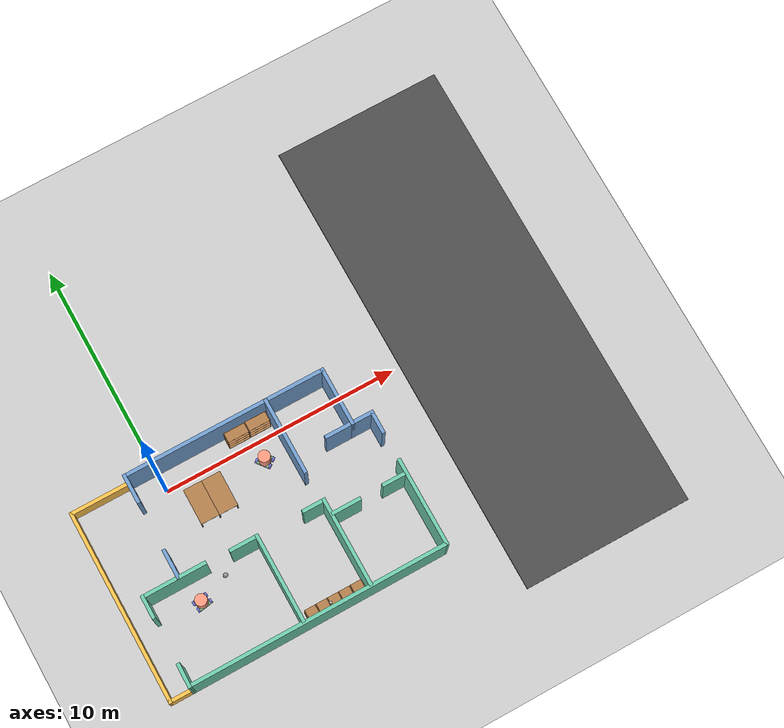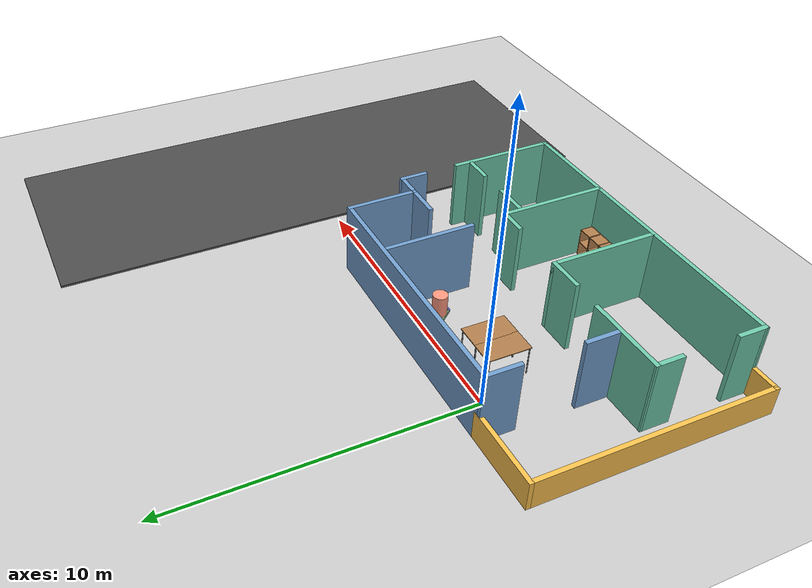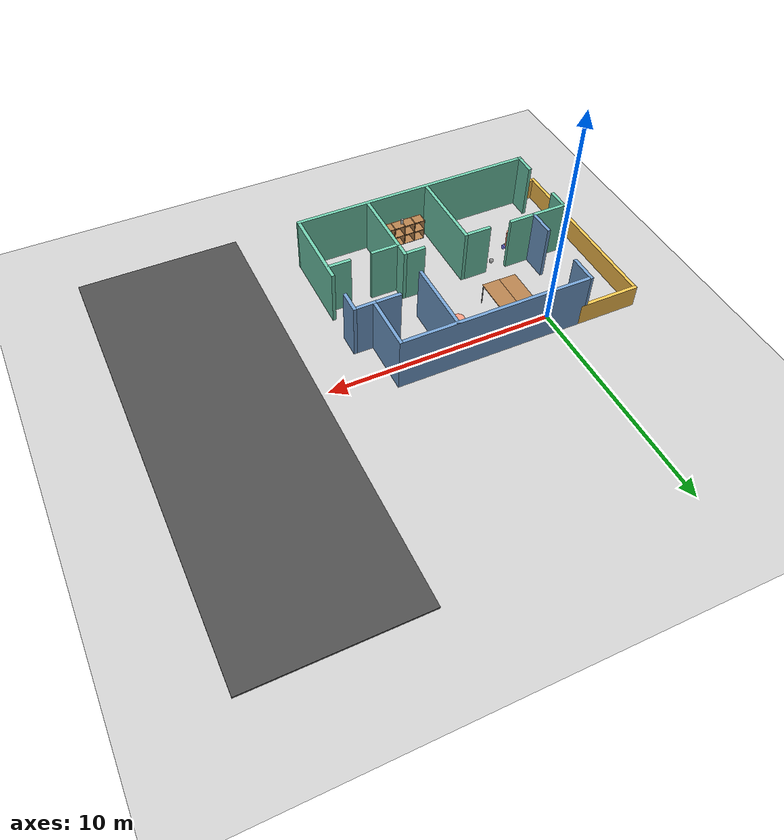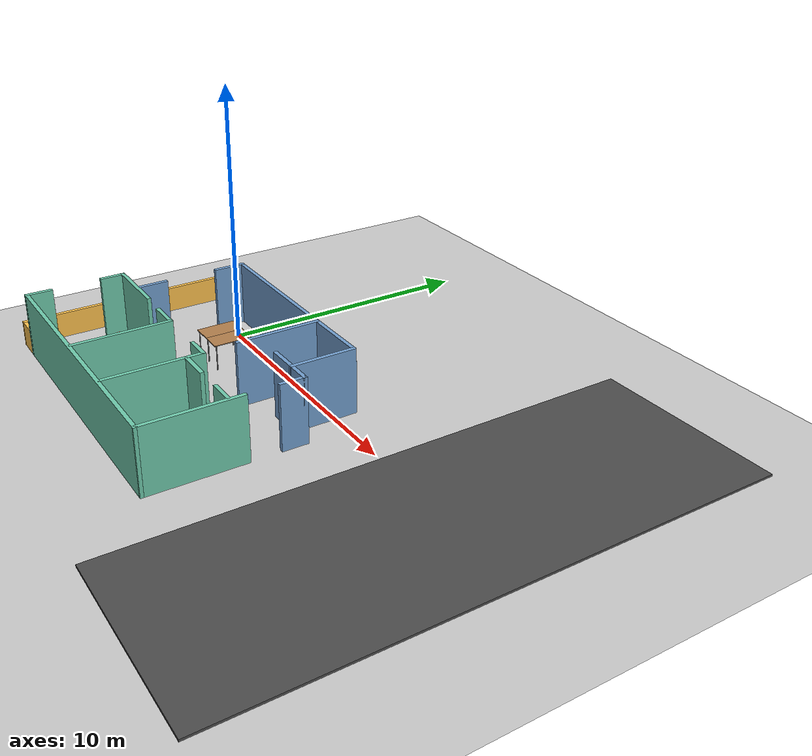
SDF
<sdf version="1.7">
 <world name="default">
  <light name="sun" type="directional">
   <pose>0 0 10 0 -0 0</pose>
   <diffuse>0.8 0.8 0.8 1</diffuse>
   <specular>0.2 0.2 0.2 1</specular>
   <attenuation>
    <range>1000</range>
    <constant>0.9</constant>
    <linear>0.01</linear>
    <quadratic>0.001</quadratic>
   </attenuation>
   <direction>-0.5 0.1 -0.9</direction>
   <spot><inner_angle>0</inner_angle><outer_angle>0</outer_angle><falloff>0</falloff></spot>
  </light>
  <model name="ground_plane">
   <static>1</static>
   <link name="link">
    <collision name="collision">
     <geometry><plane><normal>0 0 1</normal><size>100 100</size></plane></geometry>
     <surface>
      <contact><collide_bitmask>65535</collide_bitmask></contact>
      <friction><ode><mu>100</mu><mu2>50</mu2></ode></friction>
     </surface>
    </collision>
    <visual name="visual">
     <cast_shadows>0</cast_shadows>
     <geometry><plane><normal>0 0 1</normal><size>100 100</size></plane></geometry>
     <material>
      <script><uri>file://media/materials/scripts/gazebo.material</uri><name>Gazebo/Grey</name></script>
     </material>
    </visual>
   </link>
  </model>
  <gravity>0 0 -9.8</gravity>
  <magnetic_field>6e-06 2.3e-05 -4.2e-05</magnetic_field>
  <atmosphere type="adiabatic"/>
  <physics type="ode">
   <max_step_size>0.001</max_step_size>
   <real_time_factor>1</real_time_factor>
   <real_time_update_rate>1000</real_time_update_rate>
  </physics>
  <scene><ambient>0.4 0.4 0.4 1</ambient><background>0.7 0.7 0.7 1</background><shadows>1</shadows></scene>
  <spherical_coordinates>
   <surface_model>EARTH_WGS84</surface_model>
   <latitude_deg>0</latitude_deg>
   <longitude_deg>0</longitude_deg>
   <elevation>0</elevation>
   <heading_deg>0</heading_deg>
  </spherical_coordinates>
  <model name="Flat">
   <pose>2.29093 -3.22948 0 0 -0 0</pose>
   <link name="Wall_0">
    <collision name="Wall_0_Collision">
     <geometry><box><size>8.5 0.15 2.5</size></box></geometry>
     <pose>0 0 1.25 0 -0 0</pose>
    </collision>
    <visual name="Wall_0_Visual">
     <pose>0 0 1.25 0 -0 0</pose>
     <geometry><box><size>8.5 0.15 2.5</size></box></geometry>
     <material>
      <script><uri>file://media/materials/scripts/gazebo.material</uri><name>Gazebo/Grey</name></script>
      <ambient>0.447059 0.623529 0.811765 1</ambient>
     </material>
     <meta><layer>0</layer></meta>
    </visual>
    <pose>0.870433 4.05105 0 0 -0 0</pose>
   </link>
   <link name="Wall_1">
    <collision name="Wall_1_Collision">
     <geometry><box><size>2.5 0.15 2.5</size></box></geometry>
     <pose>0 0 1.25 0 -0 0</pose>
    </collision>
    <visual name="Wall_1_Visual">
     <pose>0 0 1.25 0 -0 0</pose>
     <geometry><box><size>2.5 0.15 2.5</size></box></geometry>
     <material>
      <script><uri>file://media/materials/scripts/gazebo.material</uri><name>Gazebo/Grey</name></script>
      <ambient>0.447059 0.623529 0.811765 1</ambient>
     </material>
     <meta><layer>0</layer></meta>
    </visual>
    <pose>5.04543 2.87604 0 0 -0 -1.5708</pose>
   </link>
   <link name="Wall_14">
    <collision name="Wall_14_Collision">
     <geometry><box><size>3.75 0.15 2.5</size></box></geometry>
     <pose>0 0 1.25 0 -0 0</pose>
    </collision>
    <visual name="Wall_14_Visual">
     <pose>0 0 1.25 0 -0 0</pose>
     <geometry><box><size>3.75 0.15 2.5</size></box></geometry>
     <material>
      <script><uri>file://media/materials/scripts/gazebo.material</uri><name>Gazebo/Grey</name></script>
      <ambient>0.435294 0.796078 0.67451 1</ambient>
     </material>
     <meta><layer>0</layer></meta>
    </visual>
    <pose>5.90427 -2.22379 0 0 -0 -1.5708</pose>
   </link>
   <link name="Wall_15">
    <collision name="Wall_15_Collision">
     <geometry><box><size>11.0131 0.15 2.5</size></box></geometry>
     <pose>0 0 1.25 0 -0 0</pose>
    </collision>
    <visual name="Wall_15_Visual">
     <pose>0 0 1.25 0 -0 0</pose>
     <geometry><box><size>11.0131 0.15 2.5</size></box></geometry>
     <material>
      <script><uri>file://media/materials/scripts/gazebo.material</uri><name>Gazebo/Grey</name></script>
      <ambient>0.435294 0.796078 0.67451 1</ambient>
     </material>
     <meta><layer>0</layer></meta>
    </visual>
    <pose>0.472849 -4.03687 0 0 -0 -3.13918</pose>
   </link>
   <link name="Wall_16">
    <collision name="Wall_16_Collision">
     <geometry><box><size>1.02626 0.15 2.5</size></box></geometry>
     <pose>0 0 1.25 0 -0 0</pose>
    </collision>
    <visual name="Wall_16_Visual">
     <pose>0 0 1.25 0 -0 0</pose>
     <geometry><box><size>1.02626 0.15 2.5</size></box></geometry>
     <material>
      <script><uri>file://media/materials/scripts/gazebo.material</uri><name>Gazebo/Grey</name></script>
      <ambient>0.435294 0.796078 0.67451 1</ambient>
     </material>
     <meta><layer>0</layer></meta>
    </visual>
    <pose>-4.95215 -3.61187 0 0 -0 1.55615</pose>
   </link>
   <link name="Wall_18">
    <collision name="Wall_18_Collision">
     <geometry><box><size>0.992854 0.15 2.5</size></box></geometry>
     <pose>0 0 1.25 0 -0 0</pose>
    </collision>
    <visual name="Wall_18_Visual">
     <pose>0 0 1.25 0 -0 0</pose>
     <geometry><box><size>0.992854 0.15 2.5</size></box></geometry>
     <material>
      <script><uri>file://media/materials/scripts/gazebo.material</uri><name>Gazebo/Grey</name></script>
      <ambient>0.435294 0.796078 0.67451 1</ambient>
     </material>
     <meta><layer>0</layer></meta>
    </visual>
    <pose>-4.94342 -0.738786 0 0 -0 1.56763</pose>
   </link>
   <link name="Wall_19">
    <collision name="Wall_19_Collision">
     <geometry><box><size>2.74734 0.15 2.5</size></box></geometry>
     <pose>0 0 1.25 0 -0 0</pose>
    </collision>
    <visual name="Wall_19_Visual">
     <pose>0 0 1.25 0 -0 0</pose>
     <geometry><box><size>2.74734 0.15 2.5</size></box></geometry>
     <material>
      <script><uri>file://media/materials/scripts/gazebo.material</uri><name>Gazebo/Grey</name></script>
      <ambient>0.435294 0.796078 0.67451 1</ambient>
     </material>
     <meta><layer>0</layer></meta>
    </visual>
    <pose>-3.64342 -0.313786 0 0 -0 0.002753</pose>
   </link>
   <link name="Wall_2">
    <collision name="Wall_2_Collision">
     <geometry><box><size>1 0.15 2.5</size></box></geometry>
     <pose>0 0 1.25 0 -0 0</pose>
    </collision>
    <visual name="Wall_2_Visual">
     <pose>0 0 1.25 0 -0 0</pose>
     <geometry><box><size>1 0.15 2.5</size></box></geometry>
     <material>
      <script><uri>file://media/materials/scripts/gazebo.material</uri><name>Gazebo/Grey</name></script>
      <ambient>0.447059 0.623529 0.811765 1</ambient>
     </material>
     <meta><layer>0</layer></meta>
    </visual>
    <pose>5.47043 1.70104 0 0 -0 0</pose>
   </link>
   <link name="Wall_21">
    <collision name="Wall_21_Collision">
     <geometry><box><size>1.25 0.15 2.5</size></box></geometry>
     <pose>0 0 1.25 0 -0 0</pose>
    </collision>
    <visual name="Wall_21_Visual">
     <pose>0 0 1.25 0 -0 0</pose>
     <geometry><box><size>1.25 0.15 2.5</size></box></geometry>
     <material>
      <script><uri>file://media/materials/scripts/gazebo.material</uri><name>Gazebo/Grey</name></script>
      <ambient>0.435294 0.796078 0.67451 1</ambient>
     </material>
     <meta><layer>0</layer></meta>
    </visual>
    <pose>-0.699511 -0.358041 0 0 -0 0</pose>
   </link>
   <link name="Wall_22">
    <collision name="Wall_22_Collision">
     <geometry><box><size>3.75 0.15 2.5</size></box></geometry>
     <pose>0 0 1.25 0 -0 0</pose>
    </collision>
    <visual name="Wall_22_Visual">
     <pose>0 0 1.25 0 -0 0</pose>
     <geometry><box><size>3.75 0.15 2.5</size></box></geometry>
     <material>
      <script><uri>file://media/materials/scripts/gazebo.material</uri><name>Gazebo/Grey</name></script>
      <ambient>0.435294 0.796078 0.67451 1</ambient>
     </material>
     <meta><layer>0</layer></meta>
    </visual>
    <pose>-0.149511 -2.15804 0 0 -0 -1.5708</pose>
   </link>
   <link name="Wall_24">
    <collision name="Wall_24_Collision">
     <geometry><box><size>1 0.15 2.5</size></box></geometry>
     <pose>0 0 1.25 0 -0 0</pose>
    </collision>
    <visual name="Wall_24_Visual">
     <pose>0 0 1.25 0 -0 0</pose>
     <geometry><box><size>1 0.15 2.5</size></box></geometry>
     <material>
      <script><uri>file://media/materials/scripts/gazebo.material</uri><name>Gazebo/Grey</name></script>
      <ambient>0.435294 0.796078 0.67451 1</ambient>
     </material>
     <meta><layer>0</layer></meta>
    </visual>
    <pose>2.26581 -0.371191 0 0 -0 0</pose>
   </link>
   <link name="Wall_25">
    <collision name="Wall_25_Collision">
     <geometry><box><size>3.75 0.15 2.5</size></box></geometry>
     <pose>0 0 1.25 0 -0 0</pose>
    </collision>
    <visual name="Wall_25_Visual">
     <pose>0 0 1.25 0 -0 0</pose>
     <geometry><box><size>3.75 0.15 2.5</size></box></geometry>
     <material>
      <script><uri>file://media/materials/scripts/gazebo.material</uri><name>Gazebo/Grey</name></script>
      <ambient>0.435294 0.796078 0.67451 1</ambient>
     </material>
     <meta><layer>0</layer></meta>
    </visual>
    <pose>2.69082 -2.17119 0 0 -0 -1.5708</pose>
   </link>
   <link name="Wall_27">
    <collision name="Wall_27_Collision">
     <geometry><box><size>1.25 0.15 2.5</size></box></geometry>
     <pose>0 0 1.25 0 -0 0</pose>
    </collision>
    <visual name="Wall_27_Visual">
     <pose>0 0 1.25 0 -0 0</pose>
     <geometry><box><size>1.25 0.15 2.5</size></box></geometry>
     <material>
      <script><uri>file://media/materials/scripts/gazebo.material</uri><name>Gazebo/Grey</name></script>
      <ambient>0.435294 0.796078 0.67451 1</ambient>
     </material>
     <meta><layer>0</layer></meta>
    </visual>
    <pose>3.31134 -0.976106 0 0 -0 0</pose>
   </link>
   <link name="Wall_29">
    <collision name="Wall_29_Collision">
     <geometry><box><size>1 0.15 2.5</size></box></geometry>
     <pose>0 0 1.25 0 -0 0</pose>
    </collision>
    <visual name="Wall_29_Visual">
     <pose>0 0 1.25 0 -0 0</pose>
     <geometry><box><size>1 0.15 2.5</size></box></geometry>
     <material>
      <script><uri>file://media/materials/scripts/gazebo.material</uri><name>Gazebo/Grey</name></script>
      <ambient>0.435294 0.796078 0.67451 1</ambient>
     </material>
     <meta><layer>0</layer></meta>
    </visual>
    <pose>5.36929 -0.949805 0 0 -0 0</pose>
   </link>
   <link name="Wall_3">
    <collision name="Wall_3_Collision">
     <geometry><box><size>1 0.15 2.5</size></box></geometry>
     <pose>0 0 1.25 0 -0 0</pose>
    </collision>
    <visual name="Wall_3_Visual">
     <pose>0 0 1.25 0 -0 0</pose>
     <geometry><box><size>1 0.15 2.5</size></box></geometry>
     <material>
      <script><uri>file://media/materials/scripts/gazebo.material</uri><name>Gazebo/Grey</name></script>
      <ambient>0.447059 0.623529 0.811765 1</ambient>
     </material>
     <meta><layer>0</layer></meta>
    </visual>
    <pose>5.89543 1.27605 0 0 -0 -1.5708</pose>
   </link>
   <link name="Wall_33">
    <collision name="Wall_33_Collision">
     <geometry><box><size>3.25 0.15 2.5</size></box></geometry>
     <pose>0 0 1.25 0 -0 0</pose>
    </collision>
    <visual name="Wall_33_Visual">
     <pose>0 0 1.25 0 -0 0</pose>
     <geometry><box><size>3.25 0.15 2.5</size></box></geometry>
     <material>
      <script><uri>file://media/materials/scripts/gazebo.material</uri><name>Gazebo/Grey</name></script>
      <ambient>0.447059 0.623529 0.811765 1</ambient>
     </material>
     <meta><layer>0</layer></meta>
    </visual>
    <pose>2.59038 2.48417 0 0 -0 -1.5708</pose>
   </link>
   <link name="Wall_36">
    <collision name="Wall_36_Collision">
     <geometry><box><size>1.25 0.15 2.5</size></box></geometry>
     <pose>0 0 1.25 0 -0 0</pose>
    </collision>
    <visual name="Wall_36_Visual">
     <pose>0 0 1.25 0 -0 0</pose>
     <geometry><box><size>1.25 0.15 2.5</size></box></geometry>
     <material>
      <script><uri>file://media/materials/scripts/gazebo.material</uri><name>Gazebo/Grey</name></script>
      <ambient>0.447059 0.623529 0.811765 1</ambient>
     </material>
     <meta><layer>0</layer></meta>
    </visual>
    <pose>4.49558 1.70105 0 0 -0 3.14158</pose>
   </link>
   <link name="Wall_38">
    <collision name="Wall_38_Collision">
     <geometry><box><size>1.25 0.15 2.5</size></box></geometry>
     <pose>0 0 1.25 0 -0 0</pose>
    </collision>
    <visual name="Wall_38_Visual">
     <pose>0 0 1.25 0 -0 0</pose>
     <geometry><box><size>1.25 0.15 2.5</size></box></geometry>
     <material>
      <script><uri>file://media/materials/scripts/gazebo.material</uri><name>Gazebo/Grey</name></script>
      <ambient>0.447059 0.623529 0.811765 1</ambient>
     </material>
     <meta><layer>0</layer></meta>
    </visual>
    <pose>-3.43247 3.49732 0 0 -0 -1.5708</pose>
   </link>
   <link name="Wall_40">
    <collision name="Wall_40_Collision">
     <geometry><box><size>1.25 0.15 2.5</size></box></geometry>
     <pose>0 0 1.25 0 -0 0</pose>
    </collision>
    <visual name="Wall_40_Visual">
     <pose>0 0 1.25 0 -0 0</pose>
     <geometry><box><size>1.25 0.15 2.5</size></box></geometry>
     <material>
      <script><uri>file://media/materials/scripts/gazebo.material</uri><name>Gazebo/Grey</name></script>
      <ambient>0.447059 0.623529 0.811765 1</ambient>
     </material>
     <meta><layer>0</layer></meta>
    </visual>
    <pose>-3.44562 0.262338 0 0 -0 -1.5708</pose>
   </link>
   <link name="Wall_42">
    <collision name="Wall_42_Collision">
     <geometry><box><size>2.75 0.15 1</size></box></geometry>
     <pose>0 0 0.5 0 -0 0</pose>
    </collision>
    <visual name="Wall_42_Visual">
     <pose>0 0 0.5 0 -0 0</pose>
     <geometry><box><size>2.75 0.15 1</size></box></geometry>
     <material>
      <script><uri>file://media/materials/scripts/gazebo.material</uri><name>Gazebo/Grey</name></script>
      <ambient>1 0.764706 0.305882 1</ambient>
     </material>
     <meta><layer>0</layer></meta>
    </visual>
    <pose>-4.60457 4.05105 0 0 -0 -3.14159</pose>
   </link>
   <link name="Wall_43">
    <collision name="Wall_43_Collision">
     <geometry><box><size>8.25 0.15 1</size></box></geometry>
     <pose>0 0 0.5 0 -0 0</pose>
    </collision>
    <visual name="Wall_43_Visual">
     <pose>0 0 0.5 0 -0 0</pose>
     <geometry><box><size>8.25 0.15 1</size></box></geometry>
     <material>
      <script><uri>file://media/materials/scripts/gazebo.material</uri><name>Gazebo/Grey</name></script>
      <ambient>1 0.764706 0.305882 1</ambient>
     </material>
     <meta><layer>0</layer></meta>
    </visual>
    <pose>-5.90457 0.001045 0 0 -0 -1.5708</pose>
   </link>
   <link name="Wall_46">
    <collision name="Wall_46_Collision">
     <geometry><box><size>1.09576 0.15 1</size></box></geometry>
     <pose>0 0 0.5 0 -0 0</pose>
    </collision>
    <visual name="Wall_46_Visual">
     <pose>0 0 0.5 0 -0 0</pose>
     <geometry><box><size>1.09576 0.15 1</size></box></geometry>
     <material>
      <script><uri>file://media/materials/scripts/gazebo.material</uri><name>Gazebo/Grey</name></script>
      <ambient>1 0.764706 0.305882 1</ambient>
     </material>
     <meta><layer>0</layer></meta>
    </visual>
    <pose>-5.43157 -4.04946 0 0 -0 -0.001057</pose>
   </link>
   <static>1</static>
  </model>
  <model name="cabinet">
   <static>1</static>
   <link name="cabinet_bottom_plate">
    <inertial>
     <pose>0 0 -1 0 -0 0</pose>
     <inertia><ixx>2.05</ixx><ixy>0</ixy><ixz>0</ixz><iyy>2.05</iyy><iyz>0</iyz><izz>2.05</izz></inertia>
     <mass>25</mass>
    </inertial>
    <collision name="cabinet_bottom_plate_geom">
     <pose>0 0 0.01 0 -0 0</pose>
     <geometry><box><size>0.45 0.45 0.02</size></box></geometry>
    </collision>
    <visual name="cabinet_bottom_plate_geom_visual">
     <pose>0 0 0.01 0 -0 0</pose>
     <geometry><box><size>0.45 0.45 0.02</size></box></geometry>
     <material>
      <script><uri>file://media/materials/scripts/gazebo.material</uri><name>Gazebo/Wood</name></script>
     </material>
    </visual>
    <collision name="cabinet_bottom_plate_geom_cabinet_back_plate">
     <pose>0.235 0 0.51 0 -0 0</pose>
     <geometry><box><size>0.02 0.45 1.02</size></box></geometry>
    </collision>
    <visual name="cabinet_bottom_plate_geom_cabinet_back_plate_visual">
     <pose>0.235 0 0.51 0 -0 0</pose>
     <geometry><box><size>0.02 0.45 1.02</size></box></geometry>
     <material>
      <script><uri>file://media/materials/scripts/gazebo.material</uri><name>Gazebo/Wood</name></script>
     </material>
    </visual>
    <collision name="cabinet_bottom_plate_geom_cabinet_left_plate">
     <pose>0 0.235 0.51 0 -0 0</pose>
     <geometry><box><size>0.45 0.02 1.02</size></box></geometry>
    </collision>
    <visual name="cabinet_bottom_plate_geom_cabinet_left_plate_visual">
     <pose>0 0.235 0.51 0 -0 0</pose>
     <geometry><box><size>0.45 0.02 1.02</size></box></geometry>
     <material>
      <script><uri>file://media/materials/scripts/gazebo.material</uri><name>Gazebo/Wood</name></script>
     </material>
    </visual>
    <collision name="cabinet_bottom_plate_geom_cabinet_middle_plate">
     <pose>0 0 0.51 0 -0 0</pose>
     <geometry><box><size>0.45 0.45 0.02</size></box></geometry>
    </collision>
    <visual name="cabinet_bottom_plate_geom_cabinet_middle_plate_visual">
     <pose>0 0 0.51 0 -0 0</pose>
     <geometry><box><size>0.45 0.45 0.02</size></box></geometry>
     <material>
      <script><uri>file://media/materials/scripts/gazebo.material</uri><name>Gazebo/Wood</name></script>
     </material>
    </visual>
    <collision name="cabinet_bottom_plate_geom_cabinet_right_plate">
     <pose>0 -0.235 0.51 0 -0 0</pose>
     <geometry><box><size>0.45 0.02 1.02</size></box></geometry>
    </collision>
    <visual name="cabinet_bottom_plate_geom_cabinet_right_plate_visual">
     <pose>0 -0.235 0.51 0 -0 0</pose>
     <geometry><box><size>0.45 0.02 1.02</size></box></geometry>
     <material>
      <script><uri>file://media/materials/scripts/gazebo.material</uri><name>Gazebo/Wood</name></script>
     </material>
    </visual>
    <collision name="cabinet_bottom_plate_geom_cabinet_top_plate">
     <pose>0 0 1.01 0 -0 0</pose>
     <geometry><box><size>0.45 0.45 0.02</size></box></geometry>
    </collision>
    <visual name="cabinet_bottom_plate_geom_cabinet_top_plate_visual">
     <pose>0 0 1.01 0 -0 0</pose>
     <geometry><box><size>0.45 0.45 0.02</size></box></geometry>
     <material>
      <script><uri>file://media/materials/scripts/gazebo.material</uri><name>Gazebo/Wood</name></script>
     </material>
    </visual>
   </link>
   <pose>4.6119 -6.93625 0 0 0 -1.57282</pose>
  </model>
  <model name="bookshelf">
   <static>1</static>
   <link name="link">
    <inertial><mass>1</mass></inertial>
    <collision name="back">
     <pose>0 0.005 0.6 0 -0 0</pose>
     <geometry><box><size>0.9 0.01 1.2</size></box></geometry>
    </collision>
    <visual name="visual1">
     <pose>0 0.005 0.6 0 -0 0</pose>
     <geometry><box><size>0.9 0.01 1.2</size></box></geometry>
     <material>
      <script><uri>file://media/materials/scripts/gazebo.material</uri><name>Gazebo/Wood</name></script>
     </material>
    </visual>
    <collision name="left_side">
     <pose>0.45 -0.195 0.6 0 -0 0</pose>
     <geometry><box><size>0.02 0.4 1.2</size></box></geometry>
    </collision>
    <visual name="visual2">
     <pose>0.45 -0.195 0.6 0 -0 0</pose>
     <geometry><box><size>0.02 0.4 1.2</size></box></geometry>
     <material>
      <script><uri>file://media/materials/scripts/gazebo.material</uri><name>Gazebo/Wood</name></script>
     </material>
    </visual>
    <collision name="right_side">
     <pose>-0.45 -0.195 0.6 0 -0 0</pose>
     <geometry><box><size>0.02 0.4 1.2</size></box></geometry>
    </collision>
    <visual name="visual3">
     <pose>-0.45 -0.195 0.6 0 -0 0</pose>
     <geometry><box><size>0.02 0.4 1.2</size></box></geometry>
     <material>
      <script><uri>file://media/materials/scripts/gazebo.material</uri><name>Gazebo/Wood</name></script>
     </material>
    </visual>
    <collision name="bottom">
     <pose>0 -0.195 0.03 0 -0 0</pose>
     <geometry><box><size>0.88 0.4 0.06</size></box></geometry>
    </collision>
    <visual name="visual4">
     <pose>0 -0.195 0.03 0 -0 0</pose>
     <geometry><box><size>0.88 0.4 0.06</size></box></geometry>
     <material>
      <script><uri>file://media/materials/scripts/gazebo.material</uri><name>Gazebo/Wood</name></script>
     </material>
    </visual>
    <collision name="top">
     <pose>0 -0.195 1.19 0 -0 0</pose>
     <geometry><box><size>0.88 0.4 0.02</size></box></geometry>
    </collision>
    <visual name="visual5">
     <pose>0 -0.195 1.19 0 -0 0</pose>
     <geometry><box><size>0.88 0.4 0.02</size></box></geometry>
     <material>
      <script><uri>file://media/materials/scripts/gazebo.material</uri><name>Gazebo/Wood</name></script>
     </material>
    </visual>
    <collision name="low_shelf">
     <pose>0 -0.195 0.43 0 -0 0</pose>
     <geometry><box><size>0.88 0.4 0.02</size></box></geometry>
    </collision>
    <visual name="visual6">
     <pose>0 -0.195 0.43 0 -0 0</pose>
     <geometry><box><size>0.88 0.4 0.02</size></box></geometry>
     <material>
      <script><uri>file://media/materials/scripts/gazebo.material</uri><name>Gazebo/Wood</name></script>
     </material>
    </visual>
    <collision name="high_shelf">
     <pose>0 -0.195 0.8 0 -0 0</pose>
     <geometry><box><size>0.88 0.4 0.02</size></box></geometry>
    </collision>
    <visual name="visual7">
     <pose>0 -0.195 0.8 0 -0 0</pose>
     <geometry><box><size>0.88 0.4 0.02</size></box></geometry>
     <material>
      <script><uri>file://media/materials/scripts/gazebo.material</uri><name>Gazebo/Wood</name></script>
     </material>
    </visual>
   </link>
   <pose>4.29732 0.722954 0 0 -0 0</pose>
  </model>
  <model name="table">
   <static>1</static>
   <link name="link">
    <collision name="surface">
     <pose>0 0 1 0 -0 0</pose>
     <geometry><box><size>1.5 0.8 0.03</size></box></geometry>
     <surface><friction><ode><mu>0.6</mu><mu2>0.6</mu2></ode></friction></surface>
    </collision>
    <visual name="visual1">
     <pose>0 0 1 0 -0 0</pose>
     <geometry><box><size>1.5 0.8 0.03</size></box></geometry>
     <material>
      <script><uri>file://media/materials/scripts/gazebo.material</uri><name>Gazebo/Wood</name></script>
     </material>
    </visual>
    <collision name="front_left_leg">
     <pose>0.68 0.38 0.5 0 -0 0</pose>
     <geometry><cylinder><radius>0.02</radius><length>1</length></cylinder></geometry>
    </collision>
    <visual name="front_left_leg">
     <pose>0.68 0.38 0.5 0 -0 0</pose>
     <geometry><cylinder><radius>0.02</radius><length>1</length></cylinder></geometry>
     <material>
      <script><uri>file://media/materials/scripts/gazebo.material</uri><name>Gazebo/Grey</name></script>
     </material>
    </visual>
    <collision name="front_right_leg">
     <pose>0.68 -0.38 0.5 0 -0 0</pose>
     <geometry><cylinder><radius>0.02</radius><length>1</length></cylinder></geometry>
    </collision>
    <visual name="front_right_leg">
     <pose>0.68 -0.38 0.5 0 -0 0</pose>
     <geometry><cylinder><radius>0.02</radius><length>1</length></cylinder></geometry>
     <material>
      <script><uri>file://media/materials/scripts/gazebo.material</uri><name>Gazebo/Grey</name></script>
     </material>
    </visual>
    <collision name="back_right_leg">
     <pose>-0.68 -0.38 0.5 0 -0 0</pose>
     <geometry><cylinder><radius>0.02</radius><length>1</length></cylinder></geometry>
    </collision>
    <visual name="back_right_leg">
     <pose>-0.68 -0.38 0.5 0 -0 0</pose>
     <geometry><cylinder><radius>0.02</radius><length>1</length></cylinder></geometry>
     <material>
      <script><uri>file://media/materials/scripts/gazebo.material</uri><name>Gazebo/Grey</name></script>
     </material>
    </visual>
    <collision name="back_left_leg">
     <pose>-0.68 0.38 0.5 0 -0 0</pose>
     <geometry><cylinder><radius>0.02</radius><length>1</length></cylinder></geometry>
    </collision>
    <visual name="back_left_leg">
     <pose>-0.68 0.38 0.5 0 -0 0</pose>
     <geometry><cylinder><radius>0.02</radius><length>1</length></cylinder></geometry>
     <material>
      <script><uri>file://media/materials/scripts/gazebo.material</uri><name>Gazebo/Grey</name></script>
     </material>
    </visual>
   </link>
   <pose>1.72625 -1.20385 0 0 0 -1.57665</pose>
  </model>
  <model name="beer">
   <link name="link">
    <pose>0 0 0.115 0 -0 0</pose>
    <inertial>
     <mass>0.39</mass>
     <inertia><ixx>0.00058</ixx><ixy>0</ixy><ixz>0</ixz><iyy>0.00058</iyy><iyz>0</iyz><izz>0.00019</izz></inertia>
    </inertial>
    <collision name="collision">
     <geometry><cylinder><radius>0.055</radius><length>0.23</length></cylinder></geometry>
    </collision>
    <visual name="visual">
     <geometry><cylinder><radius>0.055</radius><length>0.23</length></cylinder></geometry>
     <material>
      <script>
       <uri>model://beer/materials/scripts</uri>
       <uri>model://beer/materials/textures</uri>
       <name>Beer/Diffuse</name>
      </script>
     </material>
    </visual>
   </link>
   <pose>3.41977 -6.94915 1.02 2.2e-05 2.8e-05 0.000612</pose>
  </model>
  <model name="asphalt_plane">
   <static>1</static>
   <link name="link">
    <collision name="collision"><geometry><box><size>7.18921 20 0.1</size></box></geometry></collision>
    <visual name="visual">
     <cast_shadows>0</cast_shadows>
     <geometry><box><size>7.18921 20 0.1</size></box></geometry>
     <material>
      <script>
       <uri>model://asphalt_plane/materials/scripts</uri>
       <uri>model://asphalt_plane/materials/textures</uri>
       <name>vrc/asphalt</name>
      </script>
     </material>
    </visual>
   </link>
   <pose>13.9071 -0.010648 0 0 -0 0</pose>
  </model>
  <model name="table_clone">
   <static>1</static>
   <link name="link">
    <collision name="surface">
     <pose>0 0 1 0 -0 0</pose>
     <geometry><box><size>1.5 0.8 0.03</size></box></geometry>
     <surface><friction><ode><mu>0.6</mu><mu2>0.6</mu2></ode></friction></surface>
    </collision>
    <visual name="visual1">
     <pose>0 0 1 0 -0 0</pose>
     <geometry><box><size>1.5 0.8 0.03</size></box></geometry>
     <material>
      <script><uri>file://media/materials/scripts/gazebo.material</uri><name>Gazebo/Wood</name></script>
     </material>
    </visual>
    <collision name="front_left_leg">
     <pose>0.68 0.38 0.5 0 -0 0</pose>
     <geometry><cylinder><radius>0.02</radius><length>1</length></cylinder></geometry>
    </collision>
    <visual name="front_left_leg">
     <pose>0.68 0.38 0.5 0 -0 0</pose>
     <geometry><cylinder><radius>0.02</radius><length>1</length></cylinder></geometry>
     <material>
      <script><uri>file://media/materials/scripts/gazebo.material</uri><name>Gazebo/Grey</name></script>
     </material>
    </visual>
    <collision name="front_right_leg">
     <pose>0.68 -0.38 0.5 0 -0 0</pose>
     <geometry><cylinder><radius>0.02</radius><length>1</length></cylinder></geometry>
    </collision>
    <visual name="front_right_leg">
     <pose>0.68 -0.38 0.5 0 -0 0</pose>
     <geometry><cylinder><radius>0.02</radius><length>1</length></cylinder></geometry>
     <material>
      <script><uri>file://media/materials/scripts/gazebo.material</uri><name>Gazebo/Grey</name></script>
     </material>
    </visual>
    <collision name="back_right_leg">
     <pose>-0.68 -0.38 0.5 0 -0 0</pose>
     <geometry><cylinder><radius>0.02</radius><length>1</length></cylinder></geometry>
    </collision>
    <visual name="back_right_leg">
     <pose>-0.68 -0.38 0.5 0 -0 0</pose>
     <geometry><cylinder><radius>0.02</radius><length>1</length></cylinder></geometry>
     <material>
      <script><uri>file://media/materials/scripts/gazebo.material</uri><name>Gazebo/Grey</name></script>
     </material>
    </visual>
    <collision name="back_left_leg">
     <pose>-0.68 0.38 0.5 0 -0 0</pose>
     <geometry><cylinder><radius>0.02</radius><length>1</length></cylinder></geometry>
    </collision>
    <visual name="back_left_leg">
     <pose>-0.68 0.38 0.5 0 -0 0</pose>
     <geometry><cylinder><radius>0.02</radius><length>1</length></cylinder></geometry>
     <material>
      <script><uri>file://media/materials/scripts/gazebo.material</uri><name>Gazebo/Grey</name></script>
     </material>
    </visual>
   </link>
   <pose>0.949263 -1.19501 0 0 0 -1.57665</pose>
  </model>
  <model name="bookshelf_clone">
   <static>1</static>
   <link name="link">
    <inertial><mass>1</mass></inertial>
    <collision name="back">
     <pose>0 0.005 0.6 0 -0 0</pose>
     <geometry><box><size>0.9 0.01 1.2</size></box></geometry>
    </collision>
    <visual name="visual1">
     <pose>0 0.005 0.6 0 -0 0</pose>
     <geometry><box><size>0.9 0.01 1.2</size></box></geometry>
     <material>
      <script><uri>file://media/materials/scripts/gazebo.material</uri><name>Gazebo/Wood</name></script>
     </material>
    </visual>
    <collision name="left_side">
     <pose>0.45 -0.195 0.6 0 -0 0</pose>
     <geometry><box><size>0.02 0.4 1.2</size></box></geometry>
    </collision>
    <visual name="visual2">
     <pose>0.45 -0.195 0.6 0 -0 0</pose>
     <geometry><box><size>0.02 0.4 1.2</size></box></geometry>
     <material>
      <script><uri>file://media/materials/scripts/gazebo.material</uri><name>Gazebo/Wood</name></script>
     </material>
    </visual>
    <collision name="right_side">
     <pose>-0.45 -0.195 0.6 0 -0 0</pose>
     <geometry><box><size>0.02 0.4 1.2</size></box></geometry>
    </collision>
    <visual name="visual3">
     <pose>-0.45 -0.195 0.6 0 -0 0</pose>
     <geometry><box><size>0.02 0.4 1.2</size></box></geometry>
     <material>
      <script><uri>file://media/materials/scripts/gazebo.material</uri><name>Gazebo/Wood</name></script>
     </material>
    </visual>
    <collision name="bottom">
     <pose>0 -0.195 0.03 0 -0 0</pose>
     <geometry><box><size>0.88 0.4 0.06</size></box></geometry>
    </collision>
    <visual name="visual4">
     <pose>0 -0.195 0.03 0 -0 0</pose>
     <geometry><box><size>0.88 0.4 0.06</size></box></geometry>
     <material>
      <script><uri>file://media/materials/scripts/gazebo.material</uri><name>Gazebo/Wood</name></script>
     </material>
    </visual>
    <collision name="top">
     <pose>0 -0.195 1.19 0 -0 0</pose>
     <geometry><box><size>0.88 0.4 0.02</size></box></geometry>
    </collision>
    <visual name="visual5">
     <pose>0 -0.195 1.19 0 -0 0</pose>
     <geometry><box><size>0.88 0.4 0.02</size></box></geometry>
     <material>
      <script><uri>file://media/materials/scripts/gazebo.material</uri><name>Gazebo/Wood</name></script>
     </material>
    </visual>
    <collision name="low_shelf">
     <pose>0 -0.195 0.43 0 -0 0</pose>
     <geometry><box><size>0.88 0.4 0.02</size></box></geometry>
    </collision>
    <visual name="visual6">
     <pose>0 -0.195 0.43 0 -0 0</pose>
     <geometry><box><size>0.88 0.4 0.02</size></box></geometry>
     <material>
      <script><uri>file://media/materials/scripts/gazebo.material</uri><name>Gazebo/Wood</name></script>
     </material>
    </visual>
    <collision name="high_shelf">
     <pose>0 -0.195 0.8 0 -0 0</pose>
     <geometry><box><size>0.88 0.4 0.02</size></box></geometry>
    </collision>
    <visual name="visual7">
     <pose>0 -0.195 0.8 0 -0 0</pose>
     <geometry><box><size>0.88 0.4 0.02</size></box></geometry>
     <material>
      <script><uri>file://media/materials/scripts/gazebo.material</uri><name>Gazebo/Wood</name></script>
     </material>
    </visual>
   </link>
   <pose>3.37983 0.715936 0 0 -0 0</pose>
  </model>
  <model name="cabinet_clone">
   <static>1</static>
   <link name="cabinet_bottom_plate">
    <inertial>
     <pose>0 0 -1 0 -0 0</pose>
     <inertia><ixx>2.05</ixx><ixy>0</ixy><ixz>0</ixz><iyy>2.05</iyy><iyz>0</iyz><izz>2.05</izz></inertia>
     <mass>25</mass>
    </inertial>
    <collision name="cabinet_bottom_plate_geom">
     <pose>0 0 0.01 0 -0 0</pose>
     <geometry><box><size>0.45 0.45 0.02</size></box></geometry>
    </collision>
    <visual name="cabinet_bottom_plate_geom_visual">
     <pose>0 0 0.01 0 -0 0</pose>
     <geometry><box><size>0.45 0.45 0.02</size></box></geometry>
     <material>
      <script><uri>file://media/materials/scripts/gazebo.material</uri><name>Gazebo/Wood</name></script>
     </material>
    </visual>
    <collision name="cabinet_bottom_plate_geom_cabinet_back_plate">
     <pose>0.235 0 0.51 0 -0 0</pose>
     <geometry><box><size>0.02 0.45 1.02</size></box></geometry>
    </collision>
    <visual name="cabinet_bottom_plate_geom_cabinet_back_plate_visual">
     <pose>0.235 0 0.51 0 -0 0</pose>
     <geometry><box><size>0.02 0.45 1.02</size></box></geometry>
     <material>
      <script><uri>file://media/materials/scripts/gazebo.material</uri><name>Gazebo/Wood</name></script>
     </material>
    </visual>
    <collision name="cabinet_bottom_plate_geom_cabinet_left_plate">
     <pose>0 0.235 0.51 0 -0 0</pose>
     <geometry><box><size>0.45 0.02 1.02</size></box></geometry>
    </collision>
    <visual name="cabinet_bottom_plate_geom_cabinet_left_plate_visual">
     <pose>0 0.235 0.51 0 -0 0</pose>
     <geometry><box><size>0.45 0.02 1.02</size></box></geometry>
     <material>
      <script><uri>file://media/materials/scripts/gazebo.material</uri><name>Gazebo/Wood</name></script>
     </material>
    </visual>
    <collision name="cabinet_bottom_plate_geom_cabinet_middle_plate">
     <pose>0 0 0.51 0 -0 0</pose>
     <geometry><box><size>0.45 0.45 0.02</size></box></geometry>
    </collision>
    <visual name="cabinet_bottom_plate_geom_cabinet_middle_plate_visual">
     <pose>0 0 0.51 0 -0 0</pose>
     <geometry><box><size>0.45 0.45 0.02</size></box></geometry>
     <material>
      <script><uri>file://media/materials/scripts/gazebo.material</uri><name>Gazebo/Wood</name></script>
     </material>
    </visual>
    <collision name="cabinet_bottom_plate_geom_cabinet_right_plate">
     <pose>0 -0.235 0.51 0 -0 0</pose>
     <geometry><box><size>0.45 0.02 1.02</size></box></geometry>
    </collision>
    <visual name="cabinet_bottom_plate_geom_cabinet_right_plate_visual">
     <pose>0 -0.235 0.51 0 -0 0</pose>
     <geometry><box><size>0.45 0.02 1.02</size></box></geometry>
     <material>
      <script><uri>file://media/materials/scripts/gazebo.material</uri><name>Gazebo/Wood</name></script>
     </material>
    </visual>
    <collision name="cabinet_bottom_plate_geom_cabinet_top_plate">
     <pose>0 0 1.01 0 -0 0</pose>
     <geometry><box><size>0.45 0.45 0.02</size></box></geometry>
    </collision>
    <visual name="cabinet_bottom_plate_geom_cabinet_top_plate_visual">
     <pose>0 0 1.01 0 -0 0</pose>
     <geometry><box><size>0.45 0.45 0.02</size></box></geometry>
     <material>
      <script><uri>file://media/materials/scripts/gazebo.material</uri><name>Gazebo/Wood</name></script>
     </material>
    </visual>
   </link>
   <pose>4.11248 -6.9371 0 0 0 -1.57282</pose>
  </model>
  <model name="cabinet_clone_clone">
   <static>1</static>
   <link name="cabinet_bottom_plate">
    <inertial>
     <pose>0 0 -1 0 -0 0</pose>
     <inertia><ixx>2.05</ixx><ixy>0</ixy><ixz>0</ixz><iyy>2.05</iyy><iyz>0</iyz><izz>2.05</izz></inertia>
     <mass>25</mass>
    </inertial>
    <collision name="cabinet_bottom_plate_geom">
     <pose>0 0 0.01 0 -0 0</pose>
     <geometry><box><size>0.45 0.45 0.02</size></box></geometry>
    </collision>
    <visual name="cabinet_bottom_plate_geom_visual">
     <pose>0 0 0.01 0 -0 0</pose>
     <geometry><box><size>0.45 0.45 0.02</size></box></geometry>
     <material>
      <script><uri>file://media/materials/scripts/gazebo.material</uri><name>Gazebo/Wood</name></script>
     </material>
    </visual>
    <collision name="cabinet_bottom_plate_geom_cabinet_back_plate">
     <pose>0.235 0 0.51 0 -0 0</pose>
     <geometry><box><size>0.02 0.45 1.02</size></box></geometry>
    </collision>
    <visual name="cabinet_bottom_plate_geom_cabinet_back_plate_visual">
     <pose>0.235 0 0.51 0 -0 0</pose>
     <geometry><box><size>0.02 0.45 1.02</size></box></geometry>
     <material>
      <script><uri>file://media/materials/scripts/gazebo.material</uri><name>Gazebo/Wood</name></script>
     </material>
    </visual>
    <collision name="cabinet_bottom_plate_geom_cabinet_left_plate">
     <pose>0 0.235 0.51 0 -0 0</pose>
     <geometry><box><size>0.45 0.02 1.02</size></box></geometry>
    </collision>
    <visual name="cabinet_bottom_plate_geom_cabinet_left_plate_visual">
     <pose>0 0.235 0.51 0 -0 0</pose>
     <geometry><box><size>0.45 0.02 1.02</size></box></geometry>
     <material>
      <script><uri>file://media/materials/scripts/gazebo.material</uri><name>Gazebo/Wood</name></script>
     </material>
    </visual>
    <collision name="cabinet_bottom_plate_geom_cabinet_middle_plate">
     <pose>0 0 0.51 0 -0 0</pose>
     <geometry><box><size>0.45 0.45 0.02</size></box></geometry>
    </collision>
    <visual name="cabinet_bottom_plate_geom_cabinet_middle_plate_visual">
     <pose>0 0 0.51 0 -0 0</pose>
     <geometry><box><size>0.45 0.45 0.02</size></box></geometry>
     <material>
      <script><uri>file://media/materials/scripts/gazebo.material</uri><name>Gazebo/Wood</name></script>
     </material>
    </visual>
    <collision name="cabinet_bottom_plate_geom_cabinet_right_plate">
     <pose>0 -0.235 0.51 0 -0 0</pose>
     <geometry><box><size>0.45 0.02 1.02</size></box></geometry>
    </collision>
    <visual name="cabinet_bottom_plate_geom_cabinet_right_plate_visual">
     <pose>0 -0.235 0.51 0 -0 0</pose>
     <geometry><box><size>0.45 0.02 1.02</size></box></geometry>
     <material>
      <script><uri>file://media/materials/scripts/gazebo.material</uri><name>Gazebo/Wood</name></script>
     </material>
    </visual>
    <collision name="cabinet_bottom_plate_geom_cabinet_top_plate">
     <pose>0 0 1.01 0 -0 0</pose>
     <geometry><box><size>0.45 0.45 0.02</size></box></geometry>
    </collision>
    <visual name="cabinet_bottom_plate_geom_cabinet_top_plate_visual">
     <pose>0 0 1.01 0 -0 0</pose>
     <geometry><box><size>0.45 0.45 0.02</size></box></geometry>
     <material>
      <script><uri>file://media/materials/scripts/gazebo.material</uri><name>Gazebo/Wood</name></script>
     </material>
    </visual>
   </link>
   <pose>3.62409 -6.93787 0 0 0 -1.57282</pose>
  </model>
  <model name="cabinet_clone_clone_clone">
   <static>1</static>
   <link name="cabinet_bottom_plate">
    <inertial>
     <pose>0 0 -1 0 -0 0</pose>
     <inertia><ixx>2.05</ixx><ixy>0</ixy><ixz>0</ixz><iyy>2.05</iyy><iyz>0</iyz><izz>2.05</izz></inertia>
     <mass>25</mass>
    </inertial>
    <collision name="cabinet_bottom_plate_geom">
     <pose>0 0 0.01 0 -0 0</pose>
     <geometry><box><size>0.45 0.45 0.02</size></box></geometry>
    </collision>
    <visual name="cabinet_bottom_plate_geom_visual">
     <pose>0 0 0.01 0 -0 0</pose>
     <geometry><box><size>0.45 0.45 0.02</size></box></geometry>
     <material>
      <script><uri>file://media/materials/scripts/gazebo.material</uri><name>Gazebo/Wood</name></script>
     </material>
    </visual>
    <collision name="cabinet_bottom_plate_geom_cabinet_back_plate">
     <pose>0.235 0 0.51 0 -0 0</pose>
     <geometry><box><size>0.02 0.45 1.02</size></box></geometry>
    </collision>
    <visual name="cabinet_bottom_plate_geom_cabinet_back_plate_visual">
     <pose>0.235 0 0.51 0 -0 0</pose>
     <geometry><box><size>0.02 0.45 1.02</size></box></geometry>
     <material>
      <script><uri>file://media/materials/scripts/gazebo.material</uri><name>Gazebo/Wood</name></script>
     </material>
    </visual>
    <collision name="cabinet_bottom_plate_geom_cabinet_left_plate">
     <pose>0 0.235 0.51 0 -0 0</pose>
     <geometry><box><size>0.45 0.02 1.02</size></box></geometry>
    </collision>
    <visual name="cabinet_bottom_plate_geom_cabinet_left_plate_visual">
     <pose>0 0.235 0.51 0 -0 0</pose>
     <geometry><box><size>0.45 0.02 1.02</size></box></geometry>
     <material>
      <script><uri>file://media/materials/scripts/gazebo.material</uri><name>Gazebo/Wood</name></script>
     </material>
    </visual>
    <collision name="cabinet_bottom_plate_geom_cabinet_middle_plate">
     <pose>0 0 0.51 0 -0 0</pose>
     <geometry><box><size>0.45 0.45 0.02</size></box></geometry>
    </collision>
    <visual name="cabinet_bottom_plate_geom_cabinet_middle_plate_visual">
     <pose>0 0 0.51 0 -0 0</pose>
     <geometry><box><size>0.45 0.45 0.02</size></box></geometry>
     <material>
      <script><uri>file://media/materials/scripts/gazebo.material</uri><name>Gazebo/Wood</name></script>
     </material>
    </visual>
    <collision name="cabinet_bottom_plate_geom_cabinet_right_plate">
     <pose>0 -0.235 0.51 0 -0 0</pose>
     <geometry><box><size>0.45 0.02 1.02</size></box></geometry>
    </collision>
    <visual name="cabinet_bottom_plate_geom_cabinet_right_plate_visual">
     <pose>0 -0.235 0.51 0 -0 0</pose>
     <geometry><box><size>0.45 0.02 1.02</size></box></geometry>
     <material>
      <script><uri>file://media/materials/scripts/gazebo.material</uri><name>Gazebo/Wood</name></script>
     </material>
    </visual>
    <collision name="cabinet_bottom_plate_geom_cabinet_top_plate">
     <pose>0 0 1.01 0 -0 0</pose>
     <geometry><box><size>0.45 0.45 0.02</size></box></geometry>
    </collision>
    <visual name="cabinet_bottom_plate_geom_cabinet_top_plate_visual">
     <pose>0 0 1.01 0 -0 0</pose>
     <geometry><box><size>0.45 0.45 0.02</size></box></geometry>
     <material>
      <script><uri>file://media/materials/scripts/gazebo.material</uri><name>Gazebo/Wood</name></script>
     </material>
    </visual>
   </link>
   <pose>3.13383 -6.93787 0 0 0 -1.57282</pose>
  </model>
  <model name="cabinet_clone_clone_clone_0">
   <static>1</static>
   <link name="cabinet_bottom_plate">
    <inertial>
     <pose>0 0 -1 0 -0 0</pose>
     <inertia><ixx>2.05</ixx><ixy>0</ixy><ixz>0</ixz><iyy>2.05</iyy><iyz>0</iyz><izz>2.05</izz></inertia>
     <mass>25</mass>
    </inertial>
    <collision name="cabinet_bottom_plate_geom">
     <pose>0 0 0.01 0 -0 0</pose>
     <geometry><box><size>0.45 0.45 0.02</size></box></geometry>
    </collision>
    <visual name="cabinet_bottom_plate_geom_visual">
     <pose>0 0 0.01 0 -0 0</pose>
     <geometry><box><size>0.45 0.45 0.02</size></box></geometry>
     <material>
      <script><uri>file://media/materials/scripts/gazebo.material</uri><name>Gazebo/Wood</name></script>
     </material>
    </visual>
    <collision name="cabinet_bottom_plate_geom_cabinet_back_plate">
     <pose>0.235 0 0.51 0 -0 0</pose>
     <geometry><box><size>0.02 0.45 1.02</size></box></geometry>
    </collision>
    <visual name="cabinet_bottom_plate_geom_cabinet_back_plate_visual">
     <pose>0.235 0 0.51 0 -0 0</pose>
     <geometry><box><size>0.02 0.45 1.02</size></box></geometry>
     <material>
      <script><uri>file://media/materials/scripts/gazebo.material</uri><name>Gazebo/Wood</name></script>
     </material>
    </visual>
    <collision name="cabinet_bottom_plate_geom_cabinet_left_plate">
     <pose>0 0.235 0.51 0 -0 0</pose>
     <geometry><box><size>0.45 0.02 1.02</size></box></geometry>
    </collision>
    <visual name="cabinet_bottom_plate_geom_cabinet_left_plate_visual">
     <pose>0 0.235 0.51 0 -0 0</pose>
     <geometry><box><size>0.45 0.02 1.02</size></box></geometry>
     <material>
      <script><uri>file://media/materials/scripts/gazebo.material</uri><name>Gazebo/Wood</name></script>
     </material>
    </visual>
    <collision name="cabinet_bottom_plate_geom_cabinet_middle_plate">
     <pose>0 0 0.51 0 -0 0</pose>
     <geometry><box><size>0.45 0.45 0.02</size></box></geometry>
    </collision>
    <visual name="cabinet_bottom_plate_geom_cabinet_middle_plate_visual">
     <pose>0 0 0.51 0 -0 0</pose>
     <geometry><box><size>0.45 0.45 0.02</size></box></geometry>
     <material>
      <script><uri>file://media/materials/scripts/gazebo.material</uri><name>Gazebo/Wood</name></script>
     </material>
    </visual>
    <collision name="cabinet_bottom_plate_geom_cabinet_right_plate">
     <pose>0 -0.235 0.51 0 -0 0</pose>
     <geometry><box><size>0.45 0.02 1.02</size></box></geometry>
    </collision>
    <visual name="cabinet_bottom_plate_geom_cabinet_right_plate_visual">
     <pose>0 -0.235 0.51 0 -0 0</pose>
     <geometry><box><size>0.45 0.02 1.02</size></box></geometry>
     <material>
      <script><uri>file://media/materials/scripts/gazebo.material</uri><name>Gazebo/Wood</name></script>
     </material>
    </visual>
    <collision name="cabinet_bottom_plate_geom_cabinet_top_plate">
     <pose>0 0 1.01 0 -0 0</pose>
     <geometry><box><size>0.45 0.45 0.02</size></box></geometry>
    </collision>
    <visual name="cabinet_bottom_plate_geom_cabinet_top_plate_visual">
     <pose>0 0 1.01 0 -0 0</pose>
     <geometry><box><size>0.45 0.45 0.02</size></box></geometry>
     <material>
      <script><uri>file://media/materials/scripts/gazebo.material</uri><name>Gazebo/Wood</name></script>
     </material>
    </visual>
   </link>
   <pose>2.64131 -6.94051 0 0 0 -1.57282</pose>
  </model>
  <model name="ServiceRobot">
   <link name="link_0">
    <inertial>
     <mass>5</mass>
     <inertia>
      <ixx>0.108333</ixx>
      <ixy>0</ixy>
      <ixz>0</ixz>
      <iyy>0.108333</iyy>
      <iyz>0</iyz>
      <izz>0.208333</izz>
     </inertia>
    </inertial>
    <pose>0 1e-06 -0.062498 0 -0 0</pose>
    <visual name="visual">
     <geometry><box><size>0.5 0.5 0.1</size></box></geometry>
     <material>
      <lighting>1</lighting>
      <script><uri>file://media/materials/scripts/gazebo.material</uri><name>Gazebo/Grey</name></script>
      <shader type="pixel"><normal_map>__default__</normal_map></shader>
      <ambient>0.3 1 0.3 1</ambient>
      <diffuse>0.5 0.7 0.5 1</diffuse>
      <specular>0.01 0.01 0.01 1</specular>
      <emissive>0 0 0 1</emissive>
     </material>
    </visual>
    <collision name="collision">
     <geometry><box><size>0.5 0.5 0.1</size></box></geometry>
     <surface>
      <friction>
       <ode><mu>1</mu><mu2>1</mu2><fdir1>0 0 0</fdir1><slip1>0</slip1><slip2>0</slip2></ode>
       <torsional>
        <coefficient>1</coefficient>
        <patch_radius>0</patch_radius>
        <surface_radius>0</surface_radius>
        <use_patch_radius>1</use_patch_radius>
        <ode><slip>0</slip></ode>
       </torsional>
      </friction>
      <bounce><restitution_coefficient>0</restitution_coefficient><threshold>1e+06</threshold></bounce>
      <contact>
       <collide_without_contact>0</collide_without_contact>
       <collide_without_contact_bitmask>1</collide_without_contact_bitmask>
       <collide_bitmask>1</collide_bitmask>
       <ode>
        <soft_cfm>0</soft_cfm>
        <soft_erp>0.2</soft_erp>
        <kp>1e+13</kp>
        <kd>1</kd>
        <max_vel>0.01</max_vel>
        <min_depth>0</min_depth>
       </ode>
       <bullet>
        <split_impulse>1</split_impulse>
        <split_impulse_penetration_threshold>-0.01</split_impulse_penetration_threshold>
        <soft_cfm>0</soft_cfm>
        <soft_erp>0.2</soft_erp>
        <kp>1e+13</kp>
        <kd>1</kd>
       </bullet>
      </contact>
     </surface>
    </collision>
   </link>
   <link name="link_1">
    <inertial>
     <mass>5</mass>
     <inertia><ixx>0.729167</ixx><ixy>0</ixy><ixz>0</ixz><iyy>0.729167</iyy><iyz>0</iyz><izz>0.625</izz></inertia>
    </inertial>
    <pose>0 1e-06 0.312502 0 -0 0</pose>
    <visual name="visual">
     <geometry><cylinder><radius>0.25</radius><length>0.85</length></cylinder></geometry>
     <material>
      <lighting>1</lighting>
      <script><uri>file://media/materials/scripts/gazebo.material</uri><name>Gazebo/Grey</name></script>
      <shader type="pixel"><normal_map>__default__</normal_map></shader>
      <ambient>1 0.3 0.3 1</ambient>
      <diffuse>1 0.6 0.5 1</diffuse>
      <specular>0.01 0.01 0.01 1</specular>
      <emissive>0 0 0 1</emissive>
     </material>
    </visual>
    <collision name="collision">
     <geometry><cylinder><radius>0.25</radius><length>0.85</length></cylinder></geometry>
     <surface>
      <friction>
       <ode><mu>1</mu><mu2>1</mu2><fdir1>0 0 0</fdir1><slip1>0</slip1><slip2>0</slip2></ode>
       <torsional>
        <coefficient>1</coefficient>
        <patch_radius>0</patch_radius>
        <surface_radius>0</surface_radius>
        <use_patch_radius>1</use_patch_radius>
        <ode><slip>0</slip></ode>
       </torsional>
      </friction>
      <bounce><restitution_coefficient>0</restitution_coefficient><threshold>1e+06</threshold></bounce>
      <contact>
       <collide_without_contact>0</collide_without_contact>
       <collide_without_contact_bitmask>1</collide_without_contact_bitmask>
       <collide_bitmask>1</collide_bitmask>
       <ode>
        <soft_cfm>0</soft_cfm>
        <soft_erp>0.2</soft_erp>
        <kp>1e+13</kp>
        <kd>1</kd>
        <max_vel>0.01</max_vel>
        <min_depth>0</min_depth>
       </ode>
       <bullet>
        <split_impulse>1</split_impulse>
        <split_impulse_penetration_threshold>-0.01</split_impulse_penetration_threshold>
        <soft_cfm>0</soft_cfm>
        <soft_erp>0.2</soft_erp>
        <kp>1e+13</kp>
        <kd>1</kd>
       </bullet>
      </contact>
     </surface>
    </collision>
   </link>
   <link name="link_2">
    <inertial>
     <mass>1</mass>
     <inertia><ixx>0.145833</ixx><ixy>0</ixy><ixz>0</ixz><iyy>0.145833</iyy><iyz>0</iyz><izz>0.125</izz></inertia>
    </inertial>
    <pose>-0.15 -0.287513 -0.062511 1.5707 -0 0</pose>
    <visual name="visual">
     <geometry><cylinder><radius>0.1</radius><length>0.075</length></cylinder></geometry>
     <material>
      <lighting>1</lighting>
      <script><uri>file://media/materials/scripts/gazebo.material</uri><name>Gazebo/Grey</name></script>
      <shader type="pixel"><normal_map>__default__</normal_map></shader>
      <ambient>0.3 0.3 1 1</ambient>
      <diffuse>0.5 0.5 1 1</diffuse>
      <specular>0.01 0.01 0.01 1</specular>
      <emissive>0 0 0 1</emissive>
     </material>
    </visual>
    <collision name="collision">
     <geometry><cylinder><radius>0.1</radius><length>0.075</length></cylinder></geometry>
     <surface>
      <friction>
       <ode><mu>1</mu><mu2>1</mu2><fdir1>0 0 0</fdir1><slip1>0</slip1><slip2>0</slip2></ode>
       <torsional>
        <coefficient>1</coefficient>
        <patch_radius>0</patch_radius>
        <surface_radius>0</surface_radius>
        <use_patch_radius>1</use_patch_radius>
        <ode><slip>0</slip></ode>
       </torsional>
      </friction>
      <bounce><restitution_coefficient>0</restitution_coefficient><threshold>1e+06</threshold></bounce>
      <contact>
       <collide_without_contact>0</collide_without_contact>
       <collide_without_contact_bitmask>1</collide_without_contact_bitmask>
       <collide_bitmask>1</collide_bitmask>
       <ode>
        <soft_cfm>0</soft_cfm>
        <soft_erp>0.2</soft_erp>
        <kp>1e+13</kp>
        <kd>1</kd>
        <max_vel>0.01</max_vel>
        <min_depth>0</min_depth>
       </ode>
       <bullet>
        <split_impulse>1</split_impulse>
        <split_impulse_penetration_threshold>-0.01</split_impulse_penetration_threshold>
        <soft_cfm>0</soft_cfm>
        <soft_erp>0.2</soft_erp>
        <kp>1e+13</kp>
        <kd>1</kd>
       </bullet>
      </contact>
     </surface>
    </collision>
   </link>
   <link name="link_2_clone">
    <inertial>
     <mass>1</mass>
     <inertia><ixx>0.145833</ixx><ixy>0</ixy><ixz>0</ixz><iyy>0.145833</iyy><iyz>0</iyz><izz>0.125</izz></inertia>
    </inertial>
    <pose>0.15 -0.287509 -0.062498 1.5707 -0 0</pose>
    <visual name="visual">
     <geometry><cylinder><radius>0.1</radius><length>0.075</length></cylinder></geometry>
     <material>
      <lighting>1</lighting>
      <script><uri>file://media/materials/scripts/gazebo.material</uri><name>Gazebo/Grey</name></script>
      <shader type="pixel"><normal_map>__default__</normal_map></shader>
      <ambient>0.3 0.3 1 1</ambient>
      <diffuse>0.5 0.5 1 1</diffuse>
      <specular>0.01 0.01 0.01 1</specular>
      <emissive>0 0 0 1</emissive>
     </material>
    </visual>
    <collision name="collision">
     <geometry><cylinder><radius>0.1</radius><length>0.075</length></cylinder></geometry>
     <surface>
      <friction>
       <ode><mu>1</mu><mu2>1</mu2><fdir1>0 0 0</fdir1><slip1>0</slip1><slip2>0</slip2></ode>
       <torsional>
        <coefficient>1</coefficient>
        <patch_radius>0</patch_radius>
        <surface_radius>0</surface_radius>
        <use_patch_radius>1</use_patch_radius>
        <ode><slip>0</slip></ode>
       </torsional>
      </friction>
      <bounce><restitution_coefficient>0</restitution_coefficient><threshold>1e+06</threshold></bounce>
      <contact>
       <collide_without_contact>0</collide_without_contact>
       <collide_without_contact_bitmask>1</collide_without_contact_bitmask>
       <collide_bitmask>1</collide_bitmask>
       <ode>
        <soft_cfm>0</soft_cfm>
        <soft_erp>0.2</soft_erp>
        <kp>1e+13</kp>
        <kd>1</kd>
        <max_vel>0.01</max_vel>
        <min_depth>0</min_depth>
       </ode>
       <bullet>
        <split_impulse>1</split_impulse>
        <split_impulse_penetration_threshold>-0.01</split_impulse_penetration_threshold>
        <soft_cfm>0</soft_cfm>
        <soft_erp>0.2</soft_erp>
        <kp>1e+13</kp>
        <kd>1</kd>
       </bullet>
      </contact>
     </surface>
    </collision>
   </link>
   <link name="link_2_clone_0">
    <inertial>
     <mass>1</mass>
     <inertia><ixx>0.145833</ixx><ixy>0</ixy><ixz>0</ixz><iyy>0.145833</iyy><iyz>0</iyz><izz>0.125</izz></inertia>
    </inertial>
    <pose>0.15 0.28751 -0.062498 1.5707 -0 0</pose>
    <visual name="visual">
     <geometry><cylinder><radius>0.1</radius><length>0.075</length></cylinder></geometry>
     <material>
      <lighting>1</lighting>
      <script><uri>file://media/materials/scripts/gazebo.material</uri><name>Gazebo/Grey</name></script>
      <shader type="pixel"><normal_map>__default__</normal_map></shader>
      <ambient>0.3 0.3 1 1</ambient>
      <diffuse>0.5 0.5 1 1</diffuse>
      <specular>0.01 0.01 0.01 1</specular>
      <emissive>0 0 0 1</emissive>
     </material>
    </visual>
    <collision name="collision">
     <geometry><cylinder><radius>0.1</radius><length>0.075</length></cylinder></geometry>
     <surface>
      <friction>
       <ode><mu>1</mu><mu2>1</mu2><fdir1>0 0 0</fdir1><slip1>0</slip1><slip2>0</slip2></ode>
       <torsional>
        <coefficient>1</coefficient>
        <patch_radius>0</patch_radius>
        <surface_radius>0</surface_radius>
        <use_patch_radius>1</use_patch_radius>
        <ode><slip>0</slip></ode>
       </torsional>
      </friction>
      <bounce><restitution_coefficient>0</restitution_coefficient><threshold>1e+06</threshold></bounce>
      <contact>
       <collide_without_contact>0</collide_without_contact>
       <collide_without_contact_bitmask>1</collide_without_contact_bitmask>
       <collide_bitmask>1</collide_bitmask>
       <ode>
        <soft_cfm>0</soft_cfm>
        <soft_erp>0.2</soft_erp>
        <kp>1e+13</kp>
        <kd>1</kd>
        <max_vel>0.01</max_vel>
        <min_depth>0</min_depth>
       </ode>
       <bullet>
        <split_impulse>1</split_impulse>
        <split_impulse_penetration_threshold>-0.01</split_impulse_penetration_threshold>
        <soft_cfm>0</soft_cfm>
        <soft_erp>0.2</soft_erp>
        <kp>1e+13</kp>
        <kd>1</kd>
       </bullet>
      </contact>
     </surface>
    </collision>
   </link>
   <link name="link_2_clone_1">
    <inertial>
     <mass>1</mass>
     <inertia><ixx>0.145833</ixx><ixy>0</ixy><ixz>0</ixz><iyy>0.145833</iyy><iyz>0</iyz><izz>0.125</izz></inertia>
    </inertial>
    <pose>-0.15 0.28751 -0.062498 1.5707 -0 0</pose>
    <visual name="visual">
     <geometry><cylinder><radius>0.1</radius><length>0.075</length></cylinder></geometry>
     <material>
      <lighting>1</lighting>
      <script><uri>file://media/materials/scripts/gazebo.material</uri><name>Gazebo/Grey</name></script>
      <shader type="pixel"><normal_map>__default__</normal_map></shader>
      <ambient>0.3 0.3 1 1</ambient>
      <diffuse>0.5 0.5 1 1</diffuse>
      <specular>0.01 0.01 0.01 1</specular>
      <emissive>0 0 0 1</emissive>
     </material>
    </visual>
    <collision name="collision">
     <geometry><cylinder><radius>0.1</radius><length>0.075</length></cylinder></geometry>
     <surface>
      <friction>
       <ode><mu>1</mu><mu2>1</mu2><fdir1>0 0 0</fdir1><slip1>0</slip1><slip2>0</slip2></ode>
       <torsional>
        <coefficient>1</coefficient>
        <patch_radius>0</patch_radius>
        <surface_radius>0</surface_radius>
        <use_patch_radius>1</use_patch_radius>
        <ode><slip>0</slip></ode>
       </torsional>
      </friction>
      <bounce><restitution_coefficient>0</restitution_coefficient><threshold>1e+06</threshold></bounce>
      <contact>
       <collide_without_contact>0</collide_without_contact>
       <collide_without_contact_bitmask>1</collide_without_contact_bitmask>
       <collide_bitmask>1</collide_bitmask>
       <ode>
        <soft_cfm>0</soft_cfm>
        <soft_erp>0.2</soft_erp>
        <kp>1e+13</kp>
        <kd>1</kd>
        <max_vel>0.01</max_vel>
        <min_depth>0</min_depth>
       </ode>
       <bullet>
        <split_impulse>1</split_impulse>
        <split_impulse_penetration_threshold>-0.01</split_impulse_penetration_threshold>
        <soft_cfm>0</soft_cfm>
        <soft_erp>0.2</soft_erp>
        <kp>1e+13</kp>
        <kd>1</kd>
       </bullet>
      </contact>
     </surface>
    </collision>
   </link>
   <joint name="link_0_JOINT_0" type="fixed">
    <parent>link_0</parent>
    <child>link_1</child>
    <physics>
     <ode><limit><cfm>0</cfm><erp>0.2</erp></limit><suspension><cfm>0</cfm><erp>0.2</erp></suspension></ode>
    </physics>
   </joint>
   <joint name="link_0_JOINT_1" type="revolute">
    <parent>link_0</parent>
    <child>link_2</child>
    <axis>
     <xyz>0 0 1</xyz>
     <limit>
      <lower>-1.79769e+308</lower>
      <upper>1.79769e+308</upper>
      <effort>-1</effort>
      <velocity>-1</velocity>
     </limit>
     <dynamics>
      <spring_reference>0</spring_reference>
      <spring_stiffness>0</spring_stiffness>
      <damping>0</damping>
      <friction>0</friction>
     </dynamics>
    </axis>
    <physics>
     <ode><limit><cfm>0</cfm><erp>0.2</erp></limit><suspension><cfm>0</cfm><erp>0.2</erp></suspension></ode>
    </physics>
   </joint>
   <joint name="link_0_JOINT_4" type="revolute">
    <parent>link_0</parent>
    <child>link_2_clone</child>
    <axis>
     <xyz>0 0 1</xyz>
     <limit>
      <lower>-1.79769e+308</lower>
      <upper>1.79769e+308</upper>
      <effort>-1</effort>
      <velocity>-1</velocity>
     </limit>
     <dynamics>
      <spring_reference>0</spring_reference>
      <spring_stiffness>0</spring_stiffness>
      <damping>0</damping>
      <friction>0</friction>
     </dynamics>
    </axis>
    <physics>
     <ode><limit><cfm>0</cfm><erp>0.2</erp></limit><suspension><cfm>0</cfm><erp>0.2</erp></suspension></ode>
    </physics>
   </joint>
   <joint name="link_0_JOINT_5" type="revolute">
    <parent>link_0</parent>
    <child>link_2_clone_0</child>
    <axis>
     <xyz>-0 -0 -1</xyz>
     <limit>
      <lower>-1.79769e+308</lower>
      <upper>1.79769e+308</upper>
      <effort>-1</effort>
      <velocity>-1</velocity>
     </limit>
     <dynamics>
      <spring_reference>0</spring_reference>
      <spring_stiffness>0</spring_stiffness>
      <damping>0</damping>
      <friction>0</friction>
     </dynamics>
    </axis>
    <physics>
     <ode><limit><cfm>0</cfm><erp>0.2</erp></limit><suspension><cfm>0</cfm><erp>0.2</erp></suspension></ode>
    </physics>
   </joint>
   <joint name="link_0_JOINT_6" type="revolute">
    <parent>link_0</parent>
    <child>link_2_clone_1</child>
    <axis>
     <xyz>-0 -0 -1</xyz>
     <limit>
      <lower>-1.79769e+308</lower>
      <upper>1.79769e+308</upper>
      <effort>-1</effort>
      <velocity>-1</velocity>
     </limit>
     <dynamics>
      <spring_reference>0</spring_reference>
      <spring_stiffness>0</spring_stiffness>
      <damping>0</damping>
      <friction>0</friction>
     </dynamics>
    </axis>
    <physics>
     <ode><limit><cfm>0</cfm><erp>0.2</erp></limit><suspension><cfm>0</cfm><erp>0.2</erp></suspension></ode>
    </physics>
   </joint>
   <static>0</static>
   <pose>-0.822636 -4.45432 0.162504 3e-06 2.5e-05 -1.4183</pose>
  </model>
  <model name="ServiceRobot_clone">
   <link name="link_0">
    <inertial>
     <mass>5</mass>
     <inertia>
      <ixx>0.108333</ixx>
      <ixy>0</ixy>
      <ixz>0</ixz>
      <iyy>0.108333</iyy>
      <iyz>0</iyz>
      <izz>0.208333</izz>
     </inertia>
    </inertial>
    <pose>0 1e-06 -0.062498 0 -0 0</pose>
    <visual name="visual">
     <geometry><box><size>0.5 0.5 0.1</size></box></geometry>
     <material>
      <lighting>1</lighting>
      <script><uri>file://media/materials/scripts/gazebo.material</uri><name>Gazebo/Grey</name></script>
      <shader type="pixel"><normal_map>__default__</normal_map></shader>
      <ambient>0.3 1 0.3 1</ambient>
      <diffuse>0.5 0.7 0.5 1</diffuse>
      <specular>0.01 0.01 0.01 1</specular>
      <emissive>0 0 0 1</emissive>
     </material>
    </visual>
    <collision name="collision">
     <geometry><box><size>0.5 0.5 0.1</size></box></geometry>
     <surface>
      <friction>
       <ode><mu>1</mu><mu2>1</mu2><fdir1>0 0 0</fdir1><slip1>0</slip1><slip2>0</slip2></ode>
       <torsional>
        <coefficient>1</coefficient>
        <patch_radius>0</patch_radius>
        <surface_radius>0</surface_radius>
        <use_patch_radius>1</use_patch_radius>
        <ode><slip>0</slip></ode>
       </torsional>
      </friction>
      <bounce><restitution_coefficient>0</restitution_coefficient><threshold>1e+06</threshold></bounce>
      <contact>
       <collide_without_contact>0</collide_without_contact>
       <collide_without_contact_bitmask>1</collide_without_contact_bitmask>
       <collide_bitmask>1</collide_bitmask>
       <ode>
        <soft_cfm>0</soft_cfm>
        <soft_erp>0.2</soft_erp>
        <kp>1e+13</kp>
        <kd>1</kd>
        <max_vel>0.01</max_vel>
        <min_depth>0</min_depth>
       </ode>
       <bullet>
        <split_impulse>1</split_impulse>
        <split_impulse_penetration_threshold>-0.01</split_impulse_penetration_threshold>
        <soft_cfm>0</soft_cfm>
        <soft_erp>0.2</soft_erp>
        <kp>1e+13</kp>
        <kd>1</kd>
       </bullet>
      </contact>
     </surface>
    </collision>
   </link>
   <link name="link_1">
    <inertial>
     <mass>5</mass>
     <inertia><ixx>0.729167</ixx><ixy>0</ixy><ixz>0</ixz><iyy>0.729167</iyy><iyz>0</iyz><izz>0.625</izz></inertia>
    </inertial>
    <pose>0 1e-06 0.312502 0 -0 0</pose>
    <visual name="visual">
     <geometry><cylinder><radius>0.25</radius><length>0.85</length></cylinder></geometry>
     <material>
      <lighting>1</lighting>
      <script><uri>file://media/materials/scripts/gazebo.material</uri><name>Gazebo/Grey</name></script>
      <shader type="pixel"><normal_map>__default__</normal_map></shader>
      <ambient>1 0.3 0.3 1</ambient>
      <diffuse>1 0.6 0.5 1</diffuse>
      <specular>0.01 0.01 0.01 1</specular>
      <emissive>0 0 0 1</emissive>
     </material>
    </visual>
    <collision name="collision">
     <geometry><cylinder><radius>0.25</radius><length>0.85</length></cylinder></geometry>
     <surface>
      <friction>
       <ode><mu>1</mu><mu2>1</mu2><fdir1>0 0 0</fdir1><slip1>0</slip1><slip2>0</slip2></ode>
       <torsional>
        <coefficient>1</coefficient>
        <patch_radius>0</patch_radius>
        <surface_radius>0</surface_radius>
        <use_patch_radius>1</use_patch_radius>
        <ode><slip>0</slip></ode>
       </torsional>
      </friction>
      <bounce><restitution_coefficient>0</restitution_coefficient><threshold>1e+06</threshold></bounce>
      <contact>
       <collide_without_contact>0</collide_without_contact>
       <collide_without_contact_bitmask>1</collide_without_contact_bitmask>
       <collide_bitmask>1</collide_bitmask>
       <ode>
        <soft_cfm>0</soft_cfm>
        <soft_erp>0.2</soft_erp>
        <kp>1e+13</kp>
        <kd>1</kd>
        <max_vel>0.01</max_vel>
        <min_depth>0</min_depth>
       </ode>
       <bullet>
        <split_impulse>1</split_impulse>
        <split_impulse_penetration_threshold>-0.01</split_impulse_penetration_threshold>
        <soft_cfm>0</soft_cfm>
        <soft_erp>0.2</soft_erp>
        <kp>1e+13</kp>
        <kd>1</kd>
       </bullet>
      </contact>
     </surface>
    </collision>
   </link>
   <link name="link_2">
    <inertial>
     <mass>1</mass>
     <inertia><ixx>0.145833</ixx><ixy>0</ixy><ixz>0</ixz><iyy>0.145833</iyy><iyz>0</iyz><izz>0.125</izz></inertia>
    </inertial>
    <pose>-0.15 -0.287513 -0.062511 1.5707 -0 0</pose>
    <visual name="visual">
     <geometry><cylinder><radius>0.1</radius><length>0.075</length></cylinder></geometry>
     <material>
      <lighting>1</lighting>
      <script><uri>file://media/materials/scripts/gazebo.material</uri><name>Gazebo/Grey</name></script>
      <shader type="pixel"><normal_map>__default__</normal_map></shader>
      <ambient>0.3 0.3 1 1</ambient>
      <diffuse>0.5 0.5 1 1</diffuse>
      <specular>0.01 0.01 0.01 1</specular>
      <emissive>0 0 0 1</emissive>
     </material>
    </visual>
    <collision name="collision">
     <geometry><cylinder><radius>0.1</radius><length>0.075</length></cylinder></geometry>
     <surface>
      <friction>
       <ode><mu>1</mu><mu2>1</mu2><fdir1>0 0 0</fdir1><slip1>0</slip1><slip2>0</slip2></ode>
       <torsional>
        <coefficient>1</coefficient>
        <patch_radius>0</patch_radius>
        <surface_radius>0</surface_radius>
        <use_patch_radius>1</use_patch_radius>
        <ode><slip>0</slip></ode>
       </torsional>
      </friction>
      <bounce><restitution_coefficient>0</restitution_coefficient><threshold>1e+06</threshold></bounce>
      <contact>
       <collide_without_contact>0</collide_without_contact>
       <collide_without_contact_bitmask>1</collide_without_contact_bitmask>
       <collide_bitmask>1</collide_bitmask>
       <ode>
        <soft_cfm>0</soft_cfm>
        <soft_erp>0.2</soft_erp>
        <kp>1e+13</kp>
        <kd>1</kd>
        <max_vel>0.01</max_vel>
        <min_depth>0</min_depth>
       </ode>
       <bullet>
        <split_impulse>1</split_impulse>
        <split_impulse_penetration_threshold>-0.01</split_impulse_penetration_threshold>
        <soft_cfm>0</soft_cfm>
        <soft_erp>0.2</soft_erp>
        <kp>1e+13</kp>
        <kd>1</kd>
       </bullet>
      </contact>
     </surface>
    </collision>
   </link>
   <link name="link_2_clone">
    <inertial>
     <mass>1</mass>
     <inertia><ixx>0.145833</ixx><ixy>0</ixy><ixz>0</ixz><iyy>0.145833</iyy><iyz>0</iyz><izz>0.125</izz></inertia>
    </inertial>
    <pose>0.15 -0.287509 -0.062498 1.5707 -0 0</pose>
    <visual name="visual">
     <geometry><cylinder><radius>0.1</radius><length>0.075</length></cylinder></geometry>
     <material>
      <lighting>1</lighting>
      <script><uri>file://media/materials/scripts/gazebo.material</uri><name>Gazebo/Grey</name></script>
      <shader type="pixel"><normal_map>__default__</normal_map></shader>
      <ambient>0.3 0.3 1 1</ambient>
      <diffuse>0.5 0.5 1 1</diffuse>
      <specular>0.01 0.01 0.01 1</specular>
      <emissive>0 0 0 1</emissive>
     </material>
    </visual>
    <collision name="collision">
     <geometry><cylinder><radius>0.1</radius><length>0.075</length></cylinder></geometry>
     <surface>
      <friction>
       <ode><mu>1</mu><mu2>1</mu2><fdir1>0 0 0</fdir1><slip1>0</slip1><slip2>0</slip2></ode>
       <torsional>
        <coefficient>1</coefficient>
        <patch_radius>0</patch_radius>
        <surface_radius>0</surface_radius>
        <use_patch_radius>1</use_patch_radius>
        <ode><slip>0</slip></ode>
       </torsional>
      </friction>
      <bounce><restitution_coefficient>0</restitution_coefficient><threshold>1e+06</threshold></bounce>
      <contact>
       <collide_without_contact>0</collide_without_contact>
       <collide_without_contact_bitmask>1</collide_without_contact_bitmask>
       <collide_bitmask>1</collide_bitmask>
       <ode>
        <soft_cfm>0</soft_cfm>
        <soft_erp>0.2</soft_erp>
        <kp>1e+13</kp>
        <kd>1</kd>
        <max_vel>0.01</max_vel>
        <min_depth>0</min_depth>
       </ode>
       <bullet>
        <split_impulse>1</split_impulse>
        <split_impulse_penetration_threshold>-0.01</split_impulse_penetration_threshold>
        <soft_cfm>0</soft_cfm>
        <soft_erp>0.2</soft_erp>
        <kp>1e+13</kp>
        <kd>1</kd>
       </bullet>
      </contact>
     </surface>
    </collision>
   </link>
   <link name="link_2_clone_0">
    <inertial>
     <mass>1</mass>
     <inertia><ixx>0.145833</ixx><ixy>0</ixy><ixz>0</ixz><iyy>0.145833</iyy><iyz>0</iyz><izz>0.125</izz></inertia>
    </inertial>
    <pose>0.15 0.28751 -0.062498 1.5707 -0 0</pose>
    <visual name="visual">
     <geometry><cylinder><radius>0.1</radius><length>0.075</length></cylinder></geometry>
     <material>
      <lighting>1</lighting>
      <script><uri>file://media/materials/scripts/gazebo.material</uri><name>Gazebo/Grey</name></script>
      <shader type="pixel"><normal_map>__default__</normal_map></shader>
      <ambient>0.3 0.3 1 1</ambient>
      <diffuse>0.5 0.5 1 1</diffuse>
      <specular>0.01 0.01 0.01 1</specular>
      <emissive>0 0 0 1</emissive>
     </material>
    </visual>
    <collision name="collision">
     <geometry><cylinder><radius>0.1</radius><length>0.075</length></cylinder></geometry>
     <surface>
      <friction>
       <ode><mu>1</mu><mu2>1</mu2><fdir1>0 0 0</fdir1><slip1>0</slip1><slip2>0</slip2></ode>
       <torsional>
        <coefficient>1</coefficient>
        <patch_radius>0</patch_radius>
        <surface_radius>0</surface_radius>
        <use_patch_radius>1</use_patch_radius>
        <ode><slip>0</slip></ode>
       </torsional>
      </friction>
      <bounce><restitution_coefficient>0</restitution_coefficient><threshold>1e+06</threshold></bounce>
      <contact>
       <collide_without_contact>0</collide_without_contact>
       <collide_without_contact_bitmask>1</collide_without_contact_bitmask>
       <collide_bitmask>1</collide_bitmask>
       <ode>
        <soft_cfm>0</soft_cfm>
        <soft_erp>0.2</soft_erp>
        <kp>1e+13</kp>
        <kd>1</kd>
        <max_vel>0.01</max_vel>
        <min_depth>0</min_depth>
       </ode>
       <bullet>
        <split_impulse>1</split_impulse>
        <split_impulse_penetration_threshold>-0.01</split_impulse_penetration_threshold>
        <soft_cfm>0</soft_cfm>
        <soft_erp>0.2</soft_erp>
        <kp>1e+13</kp>
        <kd>1</kd>
       </bullet>
      </contact>
     </surface>
    </collision>
   </link>
   <link name="link_2_clone_1">
    <inertial>
     <mass>1</mass>
     <inertia><ixx>0.145833</ixx><ixy>0</ixy><ixz>0</ixz><iyy>0.145833</iyy><iyz>0</iyz><izz>0.125</izz></inertia>
    </inertial>
    <pose>-0.15 0.28751 -0.062498 1.5707 -0 0</pose>
    <visual name="visual">
     <geometry><cylinder><radius>0.1</radius><length>0.075</length></cylinder></geometry>
     <material>
      <lighting>1</lighting>
      <script><uri>file://media/materials/scripts/gazebo.material</uri><name>Gazebo/Grey</name></script>
      <shader type="pixel"><normal_map>__default__</normal_map></shader>
      <ambient>0.3 0.3 1 1</ambient>
      <diffuse>0.5 0.5 1 1</diffuse>
      <specular>0.01 0.01 0.01 1</specular>
      <emissive>0 0 0 1</emissive>
     </material>
    </visual>
    <collision name="collision">
     <geometry><cylinder><radius>0.1</radius><length>0.075</length></cylinder></geometry>
     <surface>
      <friction>
       <ode><mu>1</mu><mu2>1</mu2><fdir1>0 0 0</fdir1><slip1>0</slip1><slip2>0</slip2></ode>
       <torsional>
        <coefficient>1</coefficient>
        <patch_radius>0</patch_radius>
        <surface_radius>0</surface_radius>
        <use_patch_radius>1</use_patch_radius>
        <ode><slip>0</slip></ode>
       </torsional>
      </friction>
      <bounce><restitution_coefficient>0</restitution_coefficient><threshold>1e+06</threshold></bounce>
      <contact>
       <collide_without_contact>0</collide_without_contact>
       <collide_without_contact_bitmask>1</collide_without_contact_bitmask>
       <collide_bitmask>1</collide_bitmask>
       <ode>
        <soft_cfm>0</soft_cfm>
        <soft_erp>0.2</soft_erp>
        <kp>1e+13</kp>
        <kd>1</kd>
        <max_vel>0.01</max_vel>
        <min_depth>0</min_depth>
       </ode>
       <bullet>
        <split_impulse>1</split_impulse>
        <split_impulse_penetration_threshold>-0.01</split_impulse_penetration_threshold>
        <soft_cfm>0</soft_cfm>
        <soft_erp>0.2</soft_erp>
        <kp>1e+13</kp>
        <kd>1</kd>
       </bullet>
      </contact>
     </surface>
    </collision>
   </link>
   <joint name="link_0_JOINT_0" type="fixed">
    <parent>link_0</parent>
    <child>link_1</child>
    <physics>
     <ode><limit><cfm>0</cfm><erp>0.2</erp></limit><suspension><cfm>0</cfm><erp>0.2</erp></suspension></ode>
    </physics>
   </joint>
   <joint name="link_0_JOINT_1" type="revolute">
    <parent>link_0</parent>
    <child>link_2</child>
    <axis>
     <xyz>0 0 1</xyz>
     <limit>
      <lower>-1.79769e+308</lower>
      <upper>1.79769e+308</upper>
      <effort>-1</effort>
      <velocity>-1</velocity>
     </limit>
     <dynamics>
      <spring_reference>0</spring_reference>
      <spring_stiffness>0</spring_stiffness>
      <damping>0</damping>
      <friction>0</friction>
     </dynamics>
    </axis>
    <physics>
     <ode><limit><cfm>0</cfm><erp>0.2</erp></limit><suspension><cfm>0</cfm><erp>0.2</erp></suspension></ode>
    </physics>
   </joint>
   <joint name="link_0_JOINT_4" type="revolute">
    <parent>link_0</parent>
    <child>link_2_clone</child>
    <axis>
     <xyz>0 0 1</xyz>
     <limit>
      <lower>-1.79769e+308</lower>
      <upper>1.79769e+308</upper>
      <effort>-1</effort>
      <velocity>-1</velocity>
     </limit>
     <dynamics>
      <spring_reference>0</spring_reference>
      <spring_stiffness>0</spring_stiffness>
      <damping>0</damping>
      <friction>0</friction>
     </dynamics>
    </axis>
    <physics>
     <ode><limit><cfm>0</cfm><erp>0.2</erp></limit><suspension><cfm>0</cfm><erp>0.2</erp></suspension></ode>
    </physics>
   </joint>
   <joint name="link_0_JOINT_5" type="revolute">
    <parent>link_0</parent>
    <child>link_2_clone_0</child>
    <axis>
     <xyz>-0 -0 -1</xyz>
     <limit>
      <lower>-1.79769e+308</lower>
      <upper>1.79769e+308</upper>
      <effort>-1</effort>
      <velocity>-1</velocity>
     </limit>
     <dynamics>
      <spring_reference>0</spring_reference>
      <spring_stiffness>0</spring_stiffness>
      <damping>0</damping>
      <friction>0</friction>
     </dynamics>
    </axis>
    <physics>
     <ode><limit><cfm>0</cfm><erp>0.2</erp></limit><suspension><cfm>0</cfm><erp>0.2</erp></suspension></ode>
    </physics>
   </joint>
   <joint name="link_0_JOINT_6" type="revolute">
    <parent>link_0</parent>
    <child>link_2_clone_1</child>
    <axis>
     <xyz>-0 -0 -1</xyz>
     <limit>
      <lower>-1.79769e+308</lower>
      <upper>1.79769e+308</upper>
      <effort>-1</effort>
      <velocity>-1</velocity>
     </limit>
     <dynamics>
      <spring_reference>0</spring_reference>
      <spring_stiffness>0</spring_stiffness>
      <damping>0</damping>
      <friction>0</friction>
     </dynamics>
    </axis>
    <physics>
     <ode><limit><cfm>0</cfm><erp>0.2</erp></limit><suspension><cfm>0</cfm><erp>0.2</erp></suspension></ode>
    </physics>
   </joint>
   <static>0</static>
   <pose>3.89913 -0.741174 0.162506 -1.9e-05 2.5e-05 -2.47789</pose>
  </model>
  <model name="my_ball">
   <link name="link_0">
    <inertial>
     <mass>1</mass>
     <inertia><ixx>0.1</ixx><ixy>0</ixy><ixz>0</ixz><iyy>0.1</iyy><iyz>0</iyz><izz>0.1</izz></inertia>
    </inertial>
    <visual name="visual">
     <geometry><sphere><radius>0.1</radius></sphere></geometry>
     <material>
      <lighting>1</lighting>
      <script><uri>file://media/materials/scripts/gazebo.material</uri><name>Gazebo/Grey</name></script>
      <shader type="pixel"><normal_map>__default__</normal_map></shader>
      <ambient>1 1 1 1</ambient>
      <diffuse>1 1 1 1</diffuse>
      <specular>1 1 1 1</specular>
      <emissive>1 1 1 1</emissive>
     </material>
    </visual>
    <collision name="collision">
     <geometry><sphere><radius>0.1</radius></sphere></geometry>
     <surface>
      <friction>
       <ode><mu>1</mu><mu2>1</mu2><fdir1>0 0 0</fdir1><slip1>0</slip1><slip2>0</slip2></ode>
       <torsional>
        <coefficient>1</coefficient>
        <patch_radius>0</patch_radius>
        <surface_radius>0</surface_radius>
        <use_patch_radius>1</use_patch_radius>
        <ode><slip>0</slip></ode>
       </torsional>
      </friction>
      <bounce><restitution_coefficient>0</restitution_coefficient><threshold>1e+06</threshold></bounce>
      <contact>
       <collide_without_contact>0</collide_without_contact>
       <collide_without_contact_bitmask>1</collide_without_contact_bitmask>
       <collide_bitmask>1</collide_bitmask>
       <ode>
        <soft_cfm>0</soft_cfm>
        <soft_erp>0.2</soft_erp>
        <kp>1e+13</kp>
        <kd>1</kd>
        <max_vel>0.01</max_vel>
        <min_depth>0</min_depth>
       </ode>
       <bullet>
        <split_impulse>1</split_impulse>
        <split_impulse_penetration_threshold>-0.01</split_impulse_penetration_threshold>
        <soft_cfm>0</soft_cfm>
        <soft_erp>0.2</soft_erp>
        <kp>1e+13</kp>
        <kd>1</kd>
       </bullet>
      </contact>
     </surface>
    </collision>
   </link>
   <static>0</static>
   <pose>0.44159 -3.96448 0.1 0 -0 0</pose>
  </model>
 </world>
</sdf>
